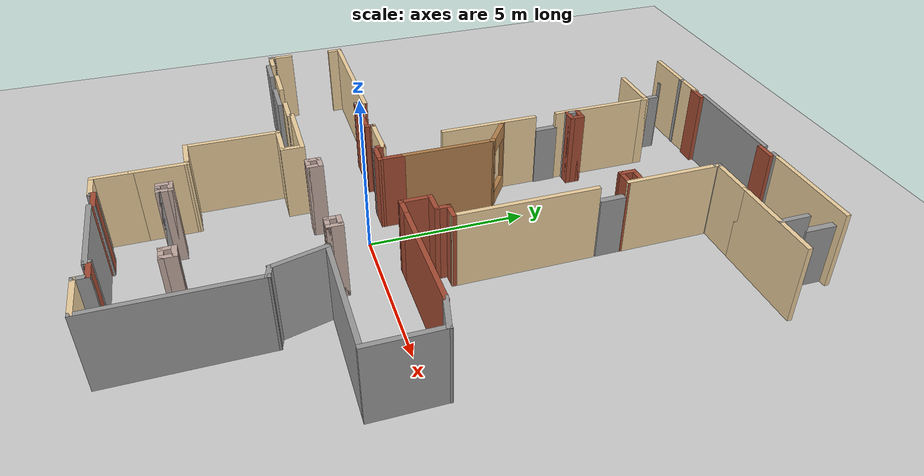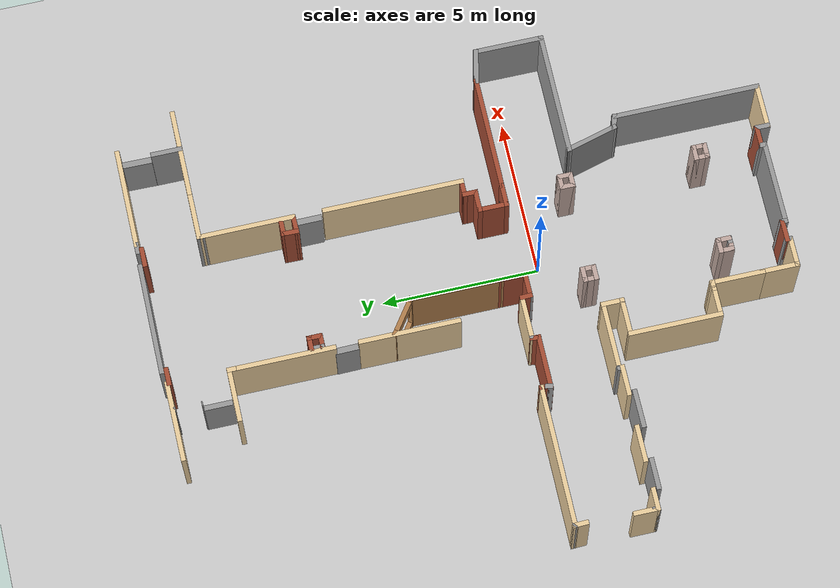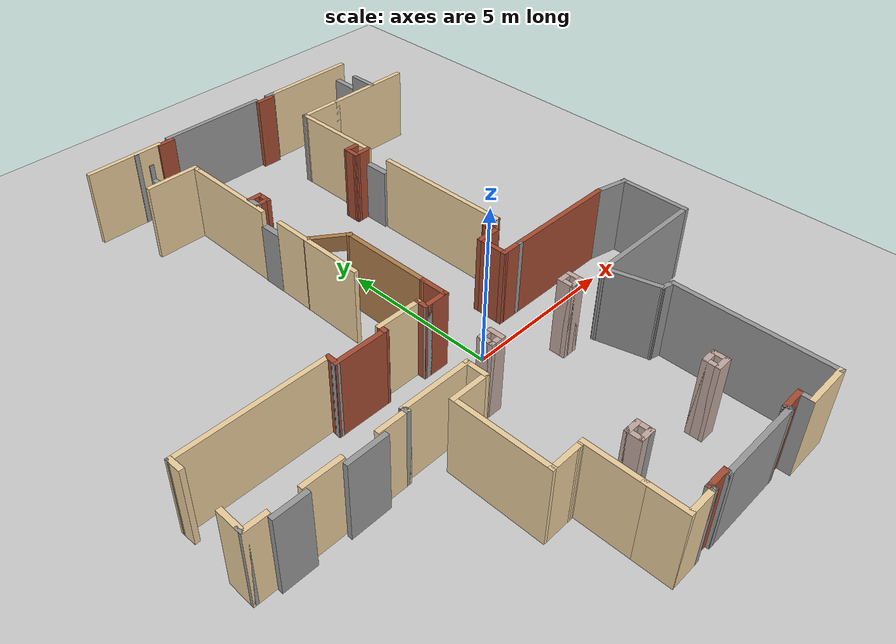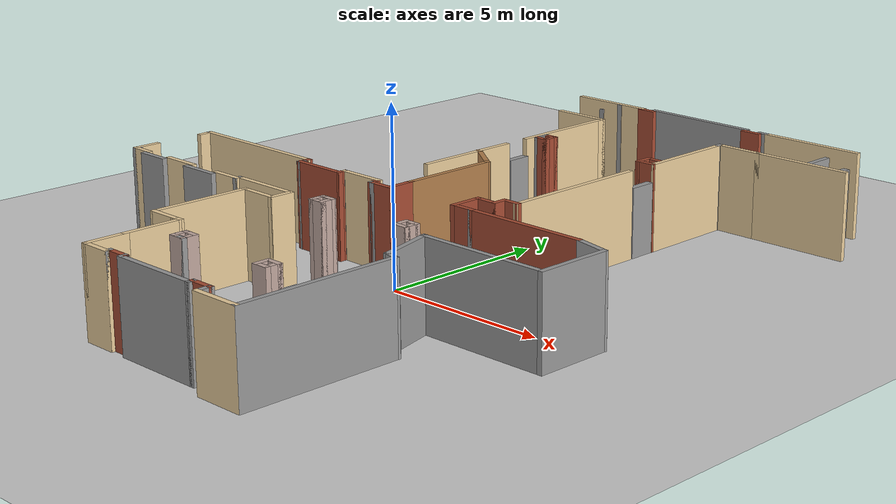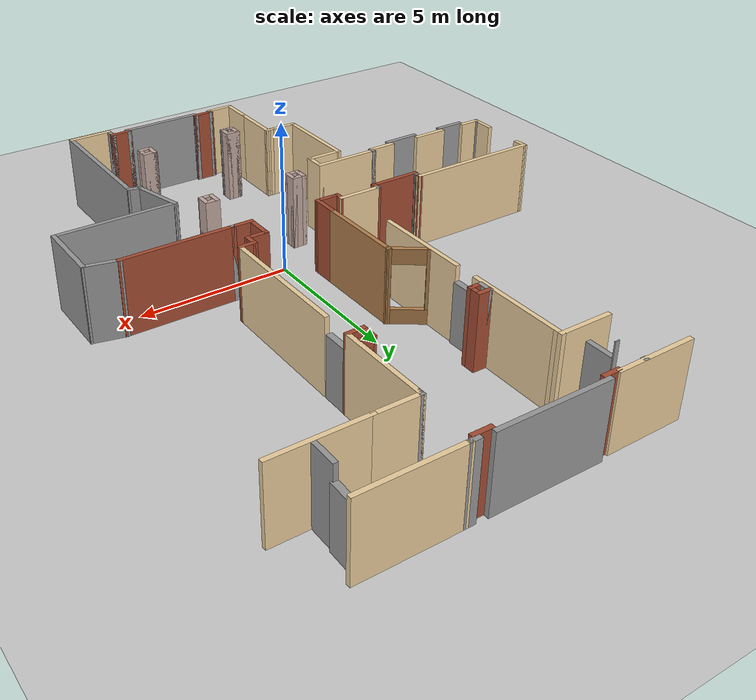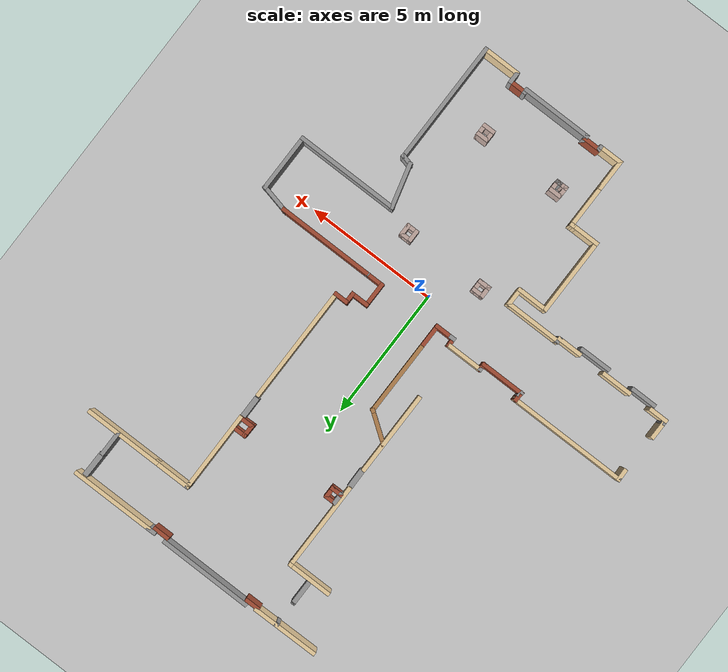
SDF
<sdf version="1.6">
 <world name="default">
  <plugin name="SpawnActorPlugin" filename="libSpawnActorPlugin.so"/>
  <model name="ground_plane">
   <static>1</static>
   <link name="link">
    <collision name="collision">
     <geometry><plane><normal>0 0 1</normal><size>100 100</size></plane></geometry>
     <surface>
      <contact><collide_bitmask>65535</collide_bitmask></contact>
      <friction><ode><mu>100</mu><mu2>50</mu2></ode></friction>
     </surface>
    </collision>
    <visual name="visual">
     <cast_shadows>0</cast_shadows>
     <geometry><plane><normal>0 0 1</normal><size>100 100</size></plane></geometry>
     <material>
      <script><uri>file://media/materials/scripts/gazebo.material</uri><name>Gazebo/Grey</name></script>
     </material>
    </visual>
   </link>
  </model>
  <gravity>0 0 -9.8</gravity>
  <magnetic_field>6e-06 2.3e-05 -4.2e-05</magnetic_field>
  <atmosphere type="adiabatic"/>
  <physics name="default_physics" default="0" type="ode">
   <max_step_size>0.001</max_step_size>
   <real_time_factor>1</real_time_factor>
   <real_time_update_rate>1000</real_time_update_rate>
  </physics>
  <scene><ambient>0.4 0.4 0.4 1</ambient><background>0.7 0.7 0.7 1</background><shadows>1</shadows></scene>
  <spherical_coordinates>
   <surface_model>EARTH_WGS84</surface_model>
   <latitude_deg>0</latitude_deg>
   <longitude_deg>0</longitude_deg>
   <elevation>0</elevation>
   <heading_deg>0</heading_deg>
  </spherical_coordinates>
  <model name="NSH_Hallway">
   <pose>-1.11426 2.16116 0 0 -0 0</pose>
   <link name="Door_5">
    <collision name="Door_5_Collision">
     <geometry><box><size>0.745301 0.2 2</size></box></geometry>
     <pose>0 0 1 0 -0 0</pose>
    </collision>
    <visual name="Door_5_Visual">
     <pose>0 0 1 0 -0 0</pose>
     <geometry><box><size>0.745301 0.2 2</size></box></geometry>
     <material>
      <script><uri>file://media/materials/scripts/gazebo.material</uri><name>Gazebo/Grey</name></script>
     </material>
    </visual>
    <pose>-0.72798 4.33452 0 0 -0 1.58636</pose>
   </link>
   <link name="Door_6">
    <collision name="Door_6_Collision">
     <geometry><box><size>0.80689 0.2 2</size></box></geometry>
     <pose>0 0 1 0 -0 0</pose>
    </collision>
    <visual name="Door_6_Visual">
     <pose>0 0 1 0 -0 0</pose>
     <geometry><box><size>0.80689 0.2 2</size></box></geometry>
     <material>
      <script><uri>file://media/materials/scripts/gazebo.material</uri><name>Gazebo/Grey</name></script>
     </material>
    </visual>
    <pose>3.65842 4.59476 0 0 -0 -1.56651</pose>
   </link>
   <link name="Door_7">
    <collision name="Door_7_Collision">
     <geometry><box><size>0.9 0.17 2</size></box></geometry>
     <pose>0 0 1 0 -0 0</pose>
    </collision>
    <visual name="Door_7_Visual">
     <pose>0 0 1 0 -0 0</pose>
     <geometry><box><size>0.9 0.17 2</size></box></geometry>
     <material>
      <script><uri>file://media/materials/scripts/gazebo.material</uri><name>Gazebo/Grey</name></script>
     </material>
    </visual>
    <pose>-1.62302 8.5531 0 0 -0 1.5718</pose>
   </link>
   <link name="Door_8">
    <collision name="Door_8_Collision">
     <geometry><box><size>1.0376 0.2 2</size></box></geometry>
     <pose>0 0 1 0 -0 0</pose>
    </collision>
    <visual name="Door_8_Visual">
     <pose>0 0 1 0 -0 0</pose>
     <geometry><box><size>1.0376 0.2 2</size></box></geometry>
     <material>
      <script><uri>file://media/materials/scripts/gazebo.material</uri><name>Gazebo/Grey</name></script>
     </material>
    </visual>
    <pose>6.70761 9.4487 0 0 -0 -1.58386</pose>
   </link>
   <link name="Wall_102">
    <collision name="Wall_102_Collision">
     <geometry><box><size>0.563182 0.15 2.5</size></box></geometry>
     <pose>0 0 1.25 0 -0 0</pose>
    </collision>
    <visual name="Wall_102_Visual">
     <pose>0 0 1.25 0 -0 0</pose>
     <geometry><box><size>0.563182 0.15 2.5</size></box></geometry>
     <material>
      <script><uri>file://media/materials/scripts/gazebo.material</uri><name>Gazebo/Bricks</name></script>
      <ambient>1 1 1 1</ambient>
     </material>
     <meta><layer>0</layer></meta>
    </visual>
    <pose>3.20361 5.2674 0 0 -0 -1.58529</pose>
   </link>
   <link name="Wall_103">
    <collision name="Wall_103_Collision">
     <geometry><box><size>0.64071 0.15 2.5</size></box></geometry>
     <pose>0 0 1.25 0 -0 0</pose>
    </collision>
    <visual name="Wall_103_Visual">
     <pose>0 0 1.25 0 -0 0</pose>
     <geometry><box><size>0.64071 0.15 2.5</size></box></geometry>
     <material>
      <script><uri>file://media/materials/scripts/gazebo.material</uri><name>Gazebo/Bricks</name></script>
      <ambient>1 1 1 1</ambient>
     </material>
     <meta><layer>0</layer></meta>
    </visual>
    <pose>3.4459 5.06699 0 0 -0 0.024385</pose>
   </link>
   <link name="Wall_105">
    <collision name="Wall_105_Collision">
     <geometry><box><size>0.75 0.15 2.5</size></box></geometry>
     <pose>0 0 1.25 0 -0 0</pose>
    </collision>
    <visual name="Wall_105_Visual">
     <pose>0 0 1.25 0 -0 0</pose>
     <geometry><box><size>0.75 0.15 2.5</size></box></geometry>
     <material>
      <script><uri>file://media/materials/scripts/gazebo.material</uri><name>Gazebo/Grey</name></script>
      <ambient>0.921569 0.807843 0.615686 1</ambient>
     </material>
     <meta><layer>0</layer></meta>
    </visual>
    <pose>-7.88142 -3.32378 0 0 -0 -1.5708</pose>
   </link>
   <link name="Wall_106">
    <collision name="Wall_106_Collision">
     <geometry><box><size>0.25 0.15 2.5</size></box></geometry>
     <pose>0 0 1.25 0 -0 0</pose>
    </collision>
    <visual name="Wall_106_Visual">
     <pose>0 0 1.25 0 -0 0</pose>
     <geometry><box><size>0.25 0.15 2.5</size></box></geometry>
     <material>
      <script><uri>file://media/materials/scripts/gazebo.material</uri><name>Gazebo/Grey</name></script>
      <ambient>1 1 1 1</ambient>
     </material>
     <meta><layer>0</layer></meta>
    </visual>
    <pose>-7.88142 -3.67378 0 0 -0 -1.5708</pose>
   </link>
   <link name="Wall_107">
    <collision name="Wall_107_Collision">
     <geometry><box><size>0.75 0.15 2.5</size></box></geometry>
     <pose>0 0 1.25 0 -0 0</pose>
    </collision>
    <visual name="Wall_107_Visual">
     <pose>0 0 1.25 0 -0 0</pose>
     <geometry><box><size>0.75 0.15 2.5</size></box></geometry>
     <material>
      <script><uri>file://media/materials/scripts/gazebo.material</uri><name>Gazebo/Grey</name></script>
      <ambient>0.921569 0.807843 0.615686 1</ambient>
     </material>
     <meta><layer>0</layer></meta>
    </visual>
    <pose>-7.58142 -3.72378 0 0 -0 0</pose>
   </link>
   <link name="Wall_109">
    <collision name="Wall_109_Collision">
     <geometry><box><size>1.19955 0.15 2.5</size></box></geometry>
     <pose>0 0 1.25 0 -0 0</pose>
    </collision>
    <visual name="Wall_109_Visual">
     <pose>0 0 1.25 0 -0 0</pose>
     <geometry><box><size>1.19955 0.15 2.5</size></box></geometry>
     <material>
      <script><uri>file://media/materials/scripts/gazebo.material</uri><name>Gazebo/Grey</name></script>
      <ambient>0.921569 0.807843 0.615686 1</ambient>
     </material>
     <meta><layer>0</layer></meta>
    </visual>
    <pose>-5.78849 -3.71137 0 0 -0 0</pose>
   </link>
   <link name="Wall_17">
    <collision name="Wall_17_Collision">
     <geometry><box><size>4.5 0.15 2.5</size></box></geometry>
     <pose>0 0 1.25 0 -0 0</pose>
    </collision>
    <visual name="Wall_17_Visual">
     <pose>0 0 1.25 0 -0 0</pose>
     <geometry><box><size>4.5 0.15 2.5</size></box></geometry>
     <material>
      <script><uri>file://media/materials/scripts/gazebo.material</uri><name>Gazebo/Grey</name></script>
      <ambient>0.921569 0.807843 0.615686 1</ambient>
     </material>
     <meta><layer>0</layer></meta>
    </visual>
    <pose>3.6845 1.90132 0 0 -0 -1.5708</pose>
   </link>
   <link name="Wall_172">
    <collision name="Wall_172_Collision">
     <geometry><box><size>1.25 0.15 2.5</size></box></geometry>
     <pose>0 0 1.25 0 -0 0</pose>
    </collision>
    <visual name="Wall_172_Visual">
     <pose>0 0 1.25 0 -0 0</pose>
     <geometry><box><size>1.25 0.15 2.5</size></box></geometry>
     <material>
      <script><uri>file://media/materials/scripts/gazebo.material</uri><name>Gazebo/Grey</name></script>
      <ambient>0.921569 0.807843 0.615686 1</ambient>
     </material>
     <meta><layer>0</layer></meta>
    </visual>
    <pose>-1.76247 -4.22776 0 0 -0 3.14144</pose>
   </link>
   <link name="Wall_173">
    <collision name="Wall_173_Collision">
     <geometry><box><size>3 0.15 2.5</size></box></geometry>
     <pose>0 0 1.25 0 -0 0</pose>
    </collision>
    <visual name="Wall_173_Visual">
     <pose>0 0 1.25 0 -0 0</pose>
     <geometry><box><size>3 0.15 2.5</size></box></geometry>
     <material>
      <script><uri>file://media/materials/scripts/gazebo.material</uri><name>Gazebo/Grey</name></script>
      <ambient>0.921569 0.807843 0.615686 1</ambient>
     </material>
     <meta><layer>0</layer></meta>
    </visual>
    <pose>-2.3125 -5.65268 0 0 -0 -1.5708</pose>
   </link>
   <link name="Wall_174">
    <collision name="Wall_174_Collision">
     <geometry><box><size>1 0.15 2.5</size></box></geometry>
     <pose>0 0 1.25 0 -0 0</pose>
    </collision>
    <visual name="Wall_174_Visual">
     <pose>0 0 1.25 0 -0 0</pose>
     <geometry><box><size>1 0.15 2.5</size></box></geometry>
     <material>
      <script><uri>file://media/materials/scripts/gazebo.material</uri><name>Gazebo/Grey</name></script>
      <ambient>0.921569 0.807843 0.615686 1</ambient>
     </material>
     <meta><layer>0</layer></meta>
    </visual>
    <pose>-1.88747 -7.07776 0 0 -0 -0.000198</pose>
   </link>
   <link name="Wall_175">
    <collision name="Wall_175_Collision">
     <geometry><box><size>0.349388 0.15 2.5</size></box></geometry>
     <pose>0 0 1.25 0 -0 0</pose>
    </collision>
    <visual name="Wall_175_Visual">
     <pose>0 0 1.25 0 -0 0</pose>
     <geometry><box><size>0.349388 0.15 2.5</size></box></geometry>
     <material>
      <script><uri>file://media/materials/scripts/gazebo.material</uri><name>Gazebo/Grey</name></script>
      <ambient>0.921569 0.807843 0.615686 1</ambient>
     </material>
     <meta><layer>0</layer></meta>
    </visual>
    <pose>-1.36276 -7.07686 0 0 -0 0.009857</pose>
   </link>
   <link name="Wall_176">
    <collision name="Wall_176_Collision">
     <geometry><box><size>1.75 0.15 2.5</size></box></geometry>
     <pose>0 0 1.25 0 -0 0</pose>
    </collision>
    <visual name="Wall_176_Visual">
     <pose>0 0 1.25 0 -0 0</pose>
     <geometry><box><size>1.75 0.15 2.5</size></box></geometry>
     <material>
      <script><uri>file://media/materials/scripts/gazebo.material</uri><name>Gazebo/Grey</name></script>
      <ambient>0.921569 0.807843 0.615686 1</ambient>
     </material>
     <meta><layer>0</layer></meta>
    </visual>
    <pose>-1.26307 -7.87588 0 0 -0 -1.5708</pose>
   </link>
   <link name="Wall_179">
    <collision name="Wall_179_Collision">
     <geometry><box><size>0.5 0.15 2.5</size></box></geometry>
     <pose>0 0 1.25 0 -0 0</pose>
    </collision>
    <visual name="Wall_179_Visual">
     <pose>0 0 1.25 0 -0 0</pose>
     <geometry><box><size>0.5 0.15 2.5</size></box></geometry>
     <material>
      <script><uri>file://media/materials/scripts/gazebo.material</uri><name>Gazebo/Grey</name></script>
      <ambient>0.760784 0.662745 0.627451 1</ambient>
     </material>
     <meta><layer>0</layer></meta>
    </visual>
    <pose>-0.146646 -7.58829 0 0 -0 0</pose>
   </link>
   <link name="Wall_180">
    <collision name="Wall_180_Collision">
     <geometry><box><size>0.5 0.15 2.5</size></box></geometry>
     <pose>0 0 1.25 0 -0 0</pose>
    </collision>
    <visual name="Wall_180_Visual">
     <pose>0 0 1.25 0 -0 0</pose>
     <geometry><box><size>0.5 0.15 2.5</size></box></geometry>
     <material>
      <script><uri>file://media/materials/scripts/gazebo.material</uri><name>Gazebo/Grey</name></script>
      <ambient>0.760784 0.662745 0.627451 1</ambient>
     </material>
     <meta><layer>0</layer></meta>
    </visual>
    <pose>0.028354 -7.76329 0 0 -0 -1.5708</pose>
   </link>
   <link name="Wall_181">
    <collision name="Wall_181_Collision">
     <geometry><box><size>0.25 0.15 2.5</size></box></geometry>
     <pose>0 0 1.25 0 -0 0</pose>
    </collision>
    <visual name="Wall_181_Visual">
     <pose>0 0 1.25 0 -0 0</pose>
     <geometry><box><size>0.25 0.15 2.5</size></box></geometry>
     <material>
      <script><uri>file://media/materials/scripts/gazebo.material</uri><name>Gazebo/Grey</name></script>
      <ambient>1 1 1 1</ambient>
     </material>
     <meta><layer>0</layer></meta>
    </visual>
    <pose>-0.021646 -7.9383 0 0 -0 3.14159</pose>
   </link>
   <link name="Wall_183">
    <collision name="Wall_183_Collision">
     <geometry><box><size>0.5 0.15 2.5</size></box></geometry>
     <pose>0 0 1.25 0 -0 0</pose>
    </collision>
    <visual name="Wall_183_Visual">
     <pose>0 0 1.25 0 -0 0</pose>
     <geometry><box><size>0.5 0.15 2.5</size></box></geometry>
     <material>
      <script><uri>file://media/materials/scripts/gazebo.material</uri><name>Gazebo/Grey</name></script>
      <ambient>0.760784 0.662745 0.627451 1</ambient>
     </material>
     <meta><layer>0</layer></meta>
    </visual>
    <pose>-0.321646 -7.76329 0 0 -0 -1.5708</pose>
   </link>
   <link name="Wall_184">
    <collision name="Wall_184_Collision">
     <geometry><box><size>0.5 0.15 2.5</size></box></geometry>
     <pose>0 0 1.25 0 -0 0</pose>
    </collision>
    <visual name="Wall_184_Visual">
     <pose>0 0 1.25 0 -0 0</pose>
     <geometry><box><size>0.5 0.15 2.5</size></box></geometry>
     <material>
      <script><uri>file://media/materials/scripts/gazebo.material</uri><name>Gazebo/Grey</name></script>
      <ambient>0.760784 0.662745 0.627451 1</ambient>
     </material>
     <meta><layer>0</layer></meta>
    </visual>
    <pose>-0.146646 -7.9383 0 0 -0 0</pose>
   </link>
   <link name="Wall_186">
    <collision name="Wall_186_Collision">
     <geometry><box><size>0.5 0.15 2.5</size></box></geometry>
     <pose>0 0 1.25 0 -0 0</pose>
    </collision>
    <visual name="Wall_186_Visual">
     <pose>0 0 1.25 0 -0 0</pose>
     <geometry><box><size>0.5 0.15 2.5</size></box></geometry>
     <material>
      <script><uri>file://media/materials/scripts/gazebo.material</uri><name>Gazebo/Grey</name></script>
      <ambient>0.760784 0.662745 0.627451 1</ambient>
     </material>
     <meta><layer>0</layer></meta>
    </visual>
    <pose>2.99841 -7.58829 0 0 -0 0</pose>
   </link>
   <link name="Wall_187">
    <collision name="Wall_187_Collision">
     <geometry><box><size>0.5 0.15 2.5</size></box></geometry>
     <pose>0 0 1.25 0 -0 0</pose>
    </collision>
    <visual name="Wall_187_Visual">
     <pose>0 0 1.25 0 -0 0</pose>
     <geometry><box><size>0.5 0.15 2.5</size></box></geometry>
     <material>
      <script><uri>file://media/materials/scripts/gazebo.material</uri><name>Gazebo/Grey</name></script>
      <ambient>0.760784 0.662745 0.627451 1</ambient>
     </material>
     <meta><layer>0</layer></meta>
    </visual>
    <pose>3.17341 -7.76329 0 0 -0 -1.5708</pose>
   </link>
   <link name="Wall_188">
    <collision name="Wall_188_Collision">
     <geometry><box><size>0.5 0.15 2.5</size></box></geometry>
     <pose>0 0 1.25 0 -0 0</pose>
    </collision>
    <visual name="Wall_188_Visual">
     <pose>0 0 1.25 0 -0 0</pose>
     <geometry><box><size>0.5 0.15 2.5</size></box></geometry>
     <material>
      <script><uri>file://media/materials/scripts/gazebo.material</uri><name>Gazebo/Grey</name></script>
      <ambient>0.760784 0.662745 0.627451 1</ambient>
     </material>
     <meta><layer>0</layer></meta>
    </visual>
    <pose>2.99841 -7.9383 0 0 -0 3.14159</pose>
   </link>
   <link name="Wall_189">
    <collision name="Wall_189_Collision">
     <geometry><box><size>0.5 0.15 2.5</size></box></geometry>
     <pose>0 0 1.25 0 -0 0</pose>
    </collision>
    <visual name="Wall_189_Visual">
     <pose>0 0 1.25 0 -0 0</pose>
     <geometry><box><size>0.5 0.15 2.5</size></box></geometry>
     <material>
      <script><uri>file://media/materials/scripts/gazebo.material</uri><name>Gazebo/Grey</name></script>
      <ambient>0.760784 0.662745 0.627451 1</ambient>
     </material>
     <meta><layer>0</layer></meta>
    </visual>
    <pose>2.82341 -7.76329 0 0 -0 1.5708</pose>
   </link>
   <link name="Wall_191">
    <collision name="Wall_191_Collision">
     <geometry><box><size>1.25 0.15 2.5</size></box></geometry>
     <pose>0 0 1.25 0 -0 0</pose>
    </collision>
    <visual name="Wall_191_Visual">
     <pose>0 0 1.25 0 -0 0</pose>
     <geometry><box><size>1.25 0.15 2.5</size></box></geometry>
     <material>
      <script><uri>file://media/materials/scripts/gazebo.material</uri><name>Gazebo/Grey</name></script>
      <ambient>0.921569 0.807843 0.615686 1</ambient>
     </material>
     <meta><layer>0</layer></meta>
    </visual>
    <pose>-1.26307 -9.22588 0 0 -0 -1.5708</pose>
   </link>
   <link name="Wall_192">
    <collision name="Wall_192_Collision">
     <geometry><box><size>1 0.15 2.5</size></box></geometry>
     <pose>0 0 1.25 0 -0 0</pose>
    </collision>
    <visual name="Wall_192_Visual">
     <pose>0 0 1.25 0 -0 0</pose>
     <geometry><box><size>1 0.15 2.5</size></box></geometry>
     <material>
      <script><uri>file://media/materials/scripts/gazebo.material</uri><name>Gazebo/Grey</name></script>
      <ambient>0.921569 0.807843 0.615686 1</ambient>
     </material>
     <meta><layer>0</layer></meta>
    </visual>
    <pose>-0.838069 -9.77588 0 0 -0 0</pose>
   </link>
   <link name="Wall_193">
    <collision name="Wall_193_Collision">
     <geometry><box><size>0.15 0.15 2.5</size></box></geometry>
     <pose>0 0 1.25 0 -0 0</pose>
    </collision>
    <visual name="Wall_193_Visual">
     <pose>0 0 1.25 0 -0 0</pose>
     <geometry><box><size>0.15 0.15 2.5</size></box></geometry>
     <material>
      <script><uri>file://media/materials/scripts/gazebo.material</uri><name>Gazebo/Grey</name></script>
      <ambient>1 1 1 1</ambient>
     </material>
     <meta><layer>0</layer></meta>
    </visual>
    <pose>-0.413069 -9.77588 0 0 -0 0</pose>
   </link>
   <link name="Wall_194">
    <collision name="Wall_194_Collision">
     <geometry><box><size>0.25 0.15 2.5</size></box></geometry>
     <pose>0 0 1.25 0 -0 0</pose>
    </collision>
    <visual name="Wall_194_Visual">
     <pose>0 0 1.25 0 -0 0</pose>
     <geometry><box><size>0.25 0.15 2.5</size></box></geometry>
     <material>
      <script><uri>file://media/materials/scripts/gazebo.material</uri><name>Gazebo/Grey</name></script>
      <ambient>1 1 1 1</ambient>
     </material>
     <meta><layer>0</layer></meta>
    </visual>
    <pose>-0.413069 -9.72588 0 0 -0 1.5708</pose>
   </link>
   <link name="Wall_195">
    <collision name="Wall_195_Collision">
     <geometry><box><size>0.75 0.15 2.5</size></box></geometry>
     <pose>0 0 1.25 0 -0 0</pose>
    </collision>
    <visual name="Wall_195_Visual">
     <pose>0 0 1.25 0 -0 0</pose>
     <geometry><box><size>0.75 0.15 2.5</size></box></geometry>
     <material>
      <script><uri>file://media/materials/scripts/gazebo.material</uri><name>Gazebo/Bricks</name></script>
      <ambient>1 1 1 1</ambient>
     </material>
     <meta><layer>0</layer></meta>
    </visual>
    <pose>-0.113069 -9.67588 0 0 -0 0</pose>
   </link>
   <link name="Wall_196">
    <collision name="Wall_196_Collision">
     <geometry><box><size>0.25 0.15 2.5</size></box></geometry>
     <pose>0 0 1.25 0 -0 0</pose>
    </collision>
    <visual name="Wall_196_Visual">
     <pose>0 0 1.25 0 -0 0</pose>
     <geometry><box><size>0.25 0.15 2.5</size></box></geometry>
     <material>
      <script><uri>file://media/materials/scripts/gazebo.material</uri><name>Gazebo/Grey</name></script>
      <ambient>1 1 1 1</ambient>
     </material>
     <meta><layer>0</layer></meta>
    </visual>
    <pose>0.186931 -9.72588 0 0 -0 -1.5708</pose>
   </link>
   <link name="Wall_197">
    <collision name="Wall_197_Collision">
     <geometry><box><size>2.75 0.15 2.5</size></box></geometry>
     <pose>0 0 1.25 0 -0 0</pose>
    </collision>
    <visual name="Wall_197_Visual">
     <pose>0 0 1.25 0 -0 0</pose>
     <geometry><box><size>2.75 0.15 2.5</size></box></geometry>
     <material>
      <script><uri>file://media/materials/scripts/gazebo.material</uri><name>Gazebo/Grey</name></script>
      <ambient>0.333333 0.341176 0.32549 1</ambient>
     </material>
     <meta><layer>0</layer></meta>
    </visual>
    <pose>1.48693 -9.77588 0 0 -0 0</pose>
   </link>
   <link name="Wall_198">
    <collision name="Wall_198_Collision">
     <geometry><box><size>0.25 0.15 2.5</size></box></geometry>
     <pose>0 0 1.25 0 -0 0</pose>
    </collision>
    <visual name="Wall_198_Visual">
     <pose>0 0 1.25 0 -0 0</pose>
     <geometry><box><size>0.25 0.15 2.5</size></box></geometry>
     <material>
      <script><uri>file://media/materials/scripts/gazebo.material</uri><name>Gazebo/Grey</name></script>
      <ambient>1 1 1 1</ambient>
     </material>
     <meta><layer>0</layer></meta>
    </visual>
    <pose>2.78693 -9.72588 0 0 -0 1.5708</pose>
   </link>
   <link name="Wall_199">
    <collision name="Wall_199_Collision">
     <geometry><box><size>0.75 0.15 2.5</size></box></geometry>
     <pose>0 0 1.25 0 -0 0</pose>
    </collision>
    <visual name="Wall_199_Visual">
     <pose>0 0 1.25 0 -0 0</pose>
     <geometry><box><size>0.75 0.15 2.5</size></box></geometry>
     <material>
      <script><uri>file://media/materials/scripts/gazebo.material</uri><name>Gazebo/Bricks</name></script>
      <ambient>1 1 1 1</ambient>
     </material>
     <meta><layer>0</layer></meta>
    </visual>
    <pose>3.08693 -9.67588 0 0 -0 0</pose>
   </link>
   <link name="Wall_20">
    <collision name="Wall_20_Collision">
     <geometry><box><size>0.597367 0.15 2.5</size></box></geometry>
     <pose>0 0 1.25 0 -0 0</pose>
    </collision>
    <visual name="Wall_20_Visual">
     <pose>0 0 1.25 0 -0 0</pose>
     <geometry><box><size>0.597367 0.15 2.5</size></box></geometry>
     <material>
      <script><uri>file://media/materials/scripts/gazebo.material</uri><name>Gazebo/Bricks</name></script>
      <ambient>1 1 1 1</ambient>
     </material>
     <meta><layer>0</layer></meta>
    </visual>
    <pose>3.461 -0.27268 0 0 -0 3.13712</pose>
   </link>
   <link name="Wall_200">
    <collision name="Wall_200_Collision">
     <geometry><box><size>0.5 0.15 2.5</size></box></geometry>
     <pose>0 0 1.25 0 -0 0</pose>
    </collision>
    <visual name="Wall_200_Visual">
     <pose>0 0 1.25 0 -0 0</pose>
     <geometry><box><size>0.5 0.15 2.5</size></box></geometry>
     <material>
      <script><uri>file://media/materials/scripts/gazebo.material</uri><name>Gazebo/Grey</name></script>
      <ambient>1 1 1 1</ambient>
     </material>
     <meta><layer>0</layer></meta>
    </visual>
    <pose>3.38693 -9.85088 0 0 -0 -1.5708</pose>
   </link>
   <link name="Wall_201">
    <collision name="Wall_201_Collision">
     <geometry><box><size>1.5 0.15 2.5</size></box></geometry>
     <pose>0 0 1.25 0 -0 0</pose>
    </collision>
    <visual name="Wall_201_Visual">
     <pose>0 0 1.25 0 -0 0</pose>
     <geometry><box><size>1.5 0.15 2.5</size></box></geometry>
     <material>
      <script><uri>file://media/materials/scripts/gazebo.material</uri><name>Gazebo/Grey</name></script>
      <ambient>0.921569 0.807843 0.615686 1</ambient>
     </material>
     <meta><layer>0</layer></meta>
    </visual>
    <pose>4.06193 -10.0259 0 0 -0 0</pose>
   </link>
   <link name="Wall_203">
    <collision name="Wall_203_Collision">
     <geometry><box><size>0.5 0.15 2.5</size></box></geometry>
     <pose>0 0 1.25 0 -0 0</pose>
    </collision>
    <visual name="Wall_203_Visual">
     <pose>0 0 1.25 0 -0 0</pose>
     <geometry><box><size>0.5 0.15 2.5</size></box></geometry>
     <material>
      <script><uri>file://media/materials/scripts/gazebo.material</uri><name>Gazebo/Grey</name></script>
      <ambient>0.760784 0.662745 0.627451 1</ambient>
     </material>
     <meta><layer>0</layer></meta>
    </visual>
    <pose>-0.14273 -3.2766 0 0 -0 0</pose>
   </link>
   <link name="Wall_204">
    <collision name="Wall_204_Collision">
     <geometry><box><size>0.5 0.15 2.5</size></box></geometry>
     <pose>0 0 1.25 0 -0 0</pose>
    </collision>
    <visual name="Wall_204_Visual">
     <pose>0 0 1.25 0 -0 0</pose>
     <geometry><box><size>0.5 0.15 2.5</size></box></geometry>
     <material>
      <script><uri>file://media/materials/scripts/gazebo.material</uri><name>Gazebo/Grey</name></script>
      <ambient>0.760784 0.662745 0.627451 1</ambient>
     </material>
     <meta><layer>0</layer></meta>
    </visual>
    <pose>0.03227 -3.4516 0 0 -0 -1.5708</pose>
   </link>
   <link name="Wall_205">
    <collision name="Wall_205_Collision">
     <geometry><box><size>0.5 0.15 2.5</size></box></geometry>
     <pose>0 0 1.25 0 -0 0</pose>
    </collision>
    <visual name="Wall_205_Visual">
     <pose>0 0 1.25 0 -0 0</pose>
     <geometry><box><size>0.5 0.15 2.5</size></box></geometry>
     <material>
      <script><uri>file://media/materials/scripts/gazebo.material</uri><name>Gazebo/Grey</name></script>
      <ambient>0.760784 0.662745 0.627451 1</ambient>
     </material>
     <meta><layer>0</layer></meta>
    </visual>
    <pose>-0.14273 -3.6266 0 0 -0 3.14159</pose>
   </link>
   <link name="Wall_206">
    <collision name="Wall_206_Collision">
     <geometry><box><size>0.5 0.15 2.5</size></box></geometry>
     <pose>0 0 1.25 0 -0 0</pose>
    </collision>
    <visual name="Wall_206_Visual">
     <pose>0 0 1.25 0 -0 0</pose>
     <geometry><box><size>0.5 0.15 2.5</size></box></geometry>
     <material>
      <script><uri>file://media/materials/scripts/gazebo.material</uri><name>Gazebo/Grey</name></script>
      <ambient>0.760784 0.662745 0.627451 1</ambient>
     </material>
     <meta><layer>0</layer></meta>
    </visual>
    <pose>-0.31773 -3.4516 0 0 -0 1.5708</pose>
   </link>
   <link name="Wall_208">
    <pose>-1.61648 9.49659 0 0 -0 -1.5708</pose>
    <visual name="Wall_208_Visual_0">
     <pose>-0.419604 0 1.25 0 -0 0</pose>
     <geometry><box><size>0.160793 0.15 2.5</size></box></geometry>
     <material>
      <script><uri>file://media/materials/scripts/gazebo.material</uri><name>Gazebo/Grey</name></script>
      <ambient>1 1 1 1</ambient>
     </material>
     <meta><layer>0</layer></meta>
    </visual>
    <collision name="Wall_208_Collision_0">
     <geometry><box><size>0.160793 0.15 2.5</size></box></geometry>
     <pose>-0.419604 0 1.25 0 -0 0</pose>
    </collision>
    <visual name="Wall_208_Visual_1">
     <pose>0.480396 0 1.25 0 -0 0</pose>
     <geometry><box><size>0.039207 0.15 2.5</size></box></geometry>
     <material>
      <script><uri>file://media/materials/scripts/gazebo.material</uri><name>Gazebo/Grey</name></script>
      <ambient>1 1 1 1</ambient>
     </material>
     <meta><layer>0</layer></meta>
    </visual>
    <collision name="Wall_208_Collision_1">
     <geometry><box><size>0.039207 0.15 2.5</size></box></geometry>
     <pose>0.480396 0 1.25 0 -0 0</pose>
    </collision>
   </link>
   <link name="Wall_21">
    <collision name="Wall_21_Collision">
     <geometry><box><size>0.5 0.15 2.5</size></box></geometry>
     <pose>0 0 1.25 0 -0 0</pose>
    </collision>
    <visual name="Wall_21_Visual">
     <pose>0 0 1.25 0 -0 0</pose>
     <geometry><box><size>0.5 0.15 2.5</size></box></geometry>
     <material>
      <script><uri>file://media/materials/scripts/gazebo.material</uri><name>Gazebo/Bricks</name></script>
      <ambient>1 1 1 1</ambient>
     </material>
     <meta><layer>0</layer></meta>
    </visual>
    <pose>3.2375 -0.44668 0 0 -0 -1.5708</pose>
   </link>
   <link name="Wall_213">
    <collision name="Wall_213_Collision">
     <geometry><box><size>1.01832 0.15 2.5</size></box></geometry>
     <pose>0 0 1.25 0 -0 0</pose>
    </collision>
    <visual name="Wall_213_Visual">
     <pose>0 0 1.25 0 -0 0</pose>
     <geometry><box><size>1.01832 0.15 2.5</size></box></geometry>
     <material>
      <script><uri>file://media/materials/scripts/gazebo.material</uri><name>Gazebo/Grey</name></script>
      <ambient>0.180392 0.203922 0.211765 1</ambient>
     </material>
     <meta><layer>0</layer></meta>
    </visual>
    <pose>-6.80225 -3.89503 0 0 -0 3.14159</pose>
   </link>
   <link name="Wall_217">
    <collision name="Wall_217_Collision">
     <geometry><box><size>1.24518 0.15 2.5</size></box></geometry>
     <pose>0 0 1.25 0 -0 0</pose>
    </collision>
    <visual name="Wall_217_Visual">
     <pose>0 0 1.25 0 -0 0</pose>
     <geometry><box><size>1.24518 0.15 2.5</size></box></geometry>
     <material>
      <script><uri>file://media/materials/scripts/gazebo.material</uri><name>Gazebo/Grey</name></script>
      <ambient>0.333333 0.341176 0.32549 1</ambient>
     </material>
     <meta><layer>0</layer></meta>
    </visual>
    <pose>-4.70184 -3.91458 0 0 -0 -3.13445</pose>
   </link>
   <link name="Wall_219">
    <collision name="Wall_219_Collision">
     <geometry><box><size>4.75 0.15 2.5</size></box></geometry>
     <pose>0 0 1.25 0 -0 0</pose>
    </collision>
    <visual name="Wall_219_Visual">
     <pose>0 0 1.25 0 -0 0</pose>
     <geometry><box><size>4.75 0.15 2.5</size></box></geometry>
     <material>
      <script><uri>file://media/materials/scripts/gazebo.material</uri><name>Gazebo/Grey</name></script>
      <ambient>0.180392 0.203922 0.211765 1</ambient>
     </material>
     <meta><layer>0</layer></meta>
    </visual>
    <pose>4.73693 -7.72588 0 0 -0 1.5708</pose>
   </link>
   <link name="Wall_22">
    <collision name="Wall_22_Collision">
     <geometry><box><size>0.75 0.15 2.5</size></box></geometry>
     <pose>0 0 1.25 0 -0 0</pose>
    </collision>
    <visual name="Wall_22_Visual">
     <pose>0 0 1.25 0 -0 0</pose>
     <geometry><box><size>0.75 0.15 2.5</size></box></geometry>
     <material>
      <script><uri>file://media/materials/scripts/gazebo.material</uri><name>Gazebo/Bricks</name></script>
      <ambient>1 1 1 1</ambient>
     </material>
     <meta><layer>0</layer></meta>
    </visual>
    <pose>2.9375 -0.62168 0 0 -0 3.14159</pose>
   </link>
   <link name="Wall_220">
    <collision name="Wall_220_Collision">
     <geometry><box><size>0.5 0.15 2.5</size></box></geometry>
     <pose>0 0 1.25 0 -0 0</pose>
    </collision>
    <visual name="Wall_220_Visual">
     <pose>0 0 1.25 0 -0 0</pose>
     <geometry><box><size>0.5 0.15 2.5</size></box></geometry>
     <material>
      <script><uri>file://media/materials/scripts/gazebo.material</uri><name>Gazebo/Grey</name></script>
      <ambient>0.180392 0.203922 0.211765 1</ambient>
     </material>
     <meta><layer>0</layer></meta>
    </visual>
    <pose>4.56789 -5.38059 0 0 -0 2.87979</pose>
   </link>
   <link name="Wall_221">
    <collision name="Wall_221_Collision">
     <geometry><box><size>1.75 0.15 2.5</size></box></geometry>
     <pose>0 0 1.25 0 -0 0</pose>
    </collision>
    <visual name="Wall_221_Visual">
     <pose>0 0 1.25 0 -0 0</pose>
     <geometry><box><size>1.75 0.15 2.5</size></box></geometry>
     <material>
      <script><uri>file://media/materials/scripts/gazebo.material</uri><name>Gazebo/Grey</name></script>
      <ambient>0.180392 0.203922 0.211765 1</ambient>
     </material>
     <meta><layer>0</layer></meta>
    </visual>
    <pose>4.1918 -4.56255 0 0 -0 1.8326</pose>
   </link>
   <link name="Wall_222">
    <collision name="Wall_222_Collision">
     <geometry><box><size>4 0.15 2.5</size></box></geometry>
     <pose>0 0 1.25 0 -0 0</pose>
    </collision>
    <visual name="Wall_222_Visual">
     <pose>0 0 1.25 0 -0 0</pose>
     <geometry><box><size>4 0.15 2.5</size></box></geometry>
     <material>
      <script><uri>file://media/materials/scripts/gazebo.material</uri><name>Gazebo/Grey</name></script>
      <ambient>0.180392 0.203922 0.211765 1</ambient>
     </material>
     <meta><layer>0</layer></meta>
    </visual>
    <pose>5.90975 -3.78981 0 0 -0 0</pose>
   </link>
   <link name="Wall_223">
    <collision name="Wall_223_Collision">
     <geometry><box><size>2.25 0.15 2.5</size></box></geometry>
     <pose>0 0 1.25 0 -0 0</pose>
    </collision>
    <visual name="Wall_223_Visual">
     <pose>0 0 1.25 0 -0 0</pose>
     <geometry><box><size>2.25 0.15 2.5</size></box></geometry>
     <material>
      <script><uri>file://media/materials/scripts/gazebo.material</uri><name>Gazebo/Grey</name></script>
      <ambient>0.180392 0.203922 0.211765 1</ambient>
     </material>
     <meta><layer>0</layer></meta>
    </visual>
    <pose>7.83475 -2.73982 0 0 -0 1.5708</pose>
   </link>
   <link name="Wall_224">
    <collision name="Wall_224_Collision">
     <geometry><box><size>1.15422 0.15 2.5</size></box></geometry>
     <pose>0 0 1.25 0 -0 0</pose>
    </collision>
    <visual name="Wall_224_Visual">
     <pose>0 0 1.25 0 -0 0</pose>
     <geometry><box><size>1.15422 0.15 2.5</size></box></geometry>
     <material>
      <script><uri>file://media/materials/scripts/gazebo.material</uri><name>Gazebo/Grey</name></script>
      <ambient>0.180392 0.203922 0.211765 1</ambient>
     </material>
     <meta><layer>0</layer></meta>
    </visual>
    <pose>7.34462 -1.58075 0 0 -0 2.92263</pose>
   </link>
   <link name="Wall_227">
    <pose>-0.233746 2.45717 0 0 -0 2.52388</pose>
    <visual name="Wall_227_Visual_0">
     <pose>-0.59521 0 1.25 0 -0 0</pose>
     <geometry><box><size>0.174603 0.15 2.5</size></box></geometry>
     <material>
      <script><uri>file://media/materials/scripts/gazebo.material</uri><name>Gazebo/Wood</name></script>
      <ambient>1 1 1 1</ambient>
     </material>
     <meta><layer>0</layer></meta>
    </visual>
    <collision name="Wall_227_Collision_0">
     <geometry><box><size>0.174603 0.15 2.5</size></box></geometry>
     <pose>-0.59521 0 1.25 0 -0 0</pose>
    </collision>
    <visual name="Wall_227_Visual_1">
     <pose>0.087302 0 0.25 0 -0 0</pose>
     <geometry><box><size>1.19042 0.15 0.5</size></box></geometry>
     <material>
      <script><uri>file://media/materials/scripts/gazebo.material</uri><name>Gazebo/Wood</name></script>
      <ambient>1 1 1 1</ambient>
     </material>
     <meta><layer>0</layer></meta>
    </visual>
    <collision name="Wall_227_Collision_1">
     <geometry><box><size>1.19042 0.15 0.5</size></box></geometry>
     <pose>0.087302 0 0.25 0 -0 0</pose>
    </collision>
    <visual name="Wall_227_Visual_2">
     <pose>0.587302 0 1.5 0 -0 0</pose>
     <geometry><box><size>0.19042 0.15 2</size></box></geometry>
     <material>
      <script><uri>file://media/materials/scripts/gazebo.material</uri><name>Gazebo/Wood</name></script>
      <ambient>1 1 1 1</ambient>
     </material>
     <meta><layer>0</layer></meta>
    </visual>
    <collision name="Wall_227_Collision_2">
     <geometry><box><size>0.19042 0.15 2</size></box></geometry>
     <pose>0.587302 0 1.5 0 -0 0</pose>
    </collision>
    <visual name="Wall_227_Visual_3">
     <pose>-0.007908 0 2.25 0 -0 0</pose>
     <geometry><box><size>1 0.15 0.5</size></box></geometry>
     <material>
      <script><uri>file://media/materials/scripts/gazebo.material</uri><name>Gazebo/Wood</name></script>
      <ambient>1 1 1 1</ambient>
     </material>
     <meta><layer>0</layer></meta>
    </visual>
    <collision name="Wall_227_Collision_3">
     <geometry><box><size>1 0.15 0.5</size></box></geometry>
     <pose>-0.007908 0 2.25 0 -0 0</pose>
    </collision>
   </link>
   <link name="Wall_23">
    <collision name="Wall_23_Collision">
     <geometry><box><size>1 0.15 2.5</size></box></geometry>
     <pose>0 0 1.25 0 -0 0</pose>
    </collision>
    <visual name="Wall_23_Visual">
     <pose>0 0 1.25 0 -0 0</pose>
     <geometry><box><size>1 0.15 2.5</size></box></geometry>
     <material>
      <script><uri>file://media/materials/scripts/gazebo.material</uri><name>Gazebo/Bricks</name></script>
      <ambient>1 1 1 1</ambient>
     </material>
     <meta><layer>0</layer></meta>
    </visual>
    <pose>2.6375 -1.04668 0 0 -0 -1.5708</pose>
   </link>
   <link name="Wall_231">
    <collision name="Wall_231_Collision">
     <geometry><box><size>3.62605 0.15 2.5</size></box></geometry>
     <pose>0 0 1.25 0 -0 0</pose>
    </collision>
    <visual name="Wall_231_Visual">
     <pose>0 0 1.25 0 -0 0</pose>
     <geometry><box><size>3.62605 0.15 2.5</size></box></geometry>
     <material>
      <script><uri>file://media/materials/scripts/gazebo.material</uri><name>Gazebo/Grey</name></script>
      <ambient>0.180392 0.203922 0.211765 1</ambient>
     </material>
     <meta><layer>0</layer></meta>
    </visual>
    <pose>1.39727 10.0188 0 0 -0 -0.003914</pose>
   </link>
   <link name="Wall_24">
    <collision name="Wall_24_Collision">
     <geometry><box><size>0.776389 0.15 2.5</size></box></geometry>
     <pose>0 0 1.25 0 -0 0</pose>
    </collision>
    <visual name="Wall_24_Visual">
     <pose>0 0 1.25 0 -0 0</pose>
     <geometry><box><size>0.776389 0.15 2.5</size></box></geometry>
     <material>
      <script><uri>file://media/materials/scripts/gazebo.material</uri><name>Gazebo/Bricks</name></script>
      <ambient>1 1 1 1</ambient>
     </material>
     <meta><layer>0</layer></meta>
    </visual>
    <pose>2.9505 -1.47168 0 0 -0 0</pose>
   </link>
   <link name="Wall_25">
    <collision name="Wall_25_Collision">
     <geometry><box><size>0.15 0.15 2.5</size></box></geometry>
     <pose>0 0 1.25 0 -0 0</pose>
    </collision>
    <visual name="Wall_25_Visual">
     <pose>0 0 1.25 0 -0 0</pose>
     <geometry><box><size>0.15 0.15 2.5</size></box></geometry>
     <material>
      <script><uri>file://media/materials/scripts/gazebo.material</uri><name>Gazebo/Grey</name></script>
      <ambient>1 1 1 1</ambient>
     </material>
     <meta><layer>0</layer></meta>
    </visual>
    <pose>3.2635 -1.47168 0 0 -0 0</pose>
   </link>
   <link name="Wall_28">
    <collision name="Wall_28_Collision">
     <geometry><box><size>3.74144 0.15 2.5</size></box></geometry>
     <pose>0 0 1.25 0 -0 0</pose>
    </collision>
    <visual name="Wall_28_Visual">
     <pose>0 0 1.25 0 -0 0</pose>
     <geometry><box><size>3.74144 0.15 2.5</size></box></geometry>
     <material>
      <script><uri>file://media/materials/scripts/gazebo.material</uri><name>Gazebo/Bricks</name></script>
      <ambient>1 1 1 1</ambient>
     </material>
     <meta><layer>0</layer></meta>
    </visual>
    <pose>5.059 -1.47168 0 0 -0 0</pose>
   </link>
   <link name="Wall_31">
    <collision name="Wall_31_Collision">
     <geometry><box><size>3 0.15 2.5</size></box></geometry>
     <pose>0 0 1.25 0 -0 0</pose>
    </collision>
    <visual name="Wall_31_Visual">
     <pose>0 0 1.25 0 -0 0</pose>
     <geometry><box><size>3 0.15 2.5</size></box></geometry>
     <material>
      <script><uri>file://media/materials/scripts/gazebo.material</uri><name>Gazebo/Wood</name></script>
      <ambient>1 1 1 1</ambient>
     </material>
     <meta><layer>0</layer></meta>
    </visual>
    <pose>0.261501 0.68032 0 0 -0 1.5708</pose>
   </link>
   <link name="Wall_33">
    <collision name="Wall_33_Collision">
     <geometry><box><size>3.22621 0.15 2.5</size></box></geometry>
     <pose>0 0 1.25 0 -0 0</pose>
    </collision>
    <visual name="Wall_33_Visual">
     <pose>0 0 1.25 0 -0 0</pose>
     <geometry><box><size>3.22621 0.15 2.5</size></box></geometry>
     <material>
      <script><uri>file://media/materials/scripts/gazebo.material</uri><name>Gazebo/Grey</name></script>
      <ambient>0.921569 0.807843 0.615686 1</ambient>
     </material>
     <meta><layer>0</layer></meta>
    </visual>
    <pose>-0.744715 2.35474 0 0 -0 -1.5708</pose>
   </link>
   <link name="Wall_35">
    <collision name="Wall_35_Collision">
     <geometry><box><size>3.27379 0.15 2.5</size></box></geometry>
     <pose>0 0 1.25 0 -0 0</pose>
    </collision>
    <visual name="Wall_35_Visual">
     <pose>0 0 1.25 0 -0 0</pose>
     <geometry><box><size>3.27379 0.15 2.5</size></box></geometry>
     <material>
      <script><uri>file://media/materials/scripts/gazebo.material</uri><name>Gazebo/Grey</name></script>
      <ambient>0.921569 0.807843 0.615686 1</ambient>
     </material>
     <meta><layer>0</layer></meta>
    </visual>
    <pose>-0.74442 6.29502 0 0 -0 1.5708</pose>
   </link>
   <link name="Wall_36">
    <collision name="Wall_36_Collision">
     <geometry><box><size>0.298475 0.15 2.5</size></box></geometry>
     <pose>0 0 1.25 0 -0 0</pose>
    </collision>
    <visual name="Wall_36_Visual">
     <pose>0 0 1.25 0 -0 0</pose>
     <geometry><box><size>0.298475 0.15 2.5</size></box></geometry>
     <material>
      <script><uri>file://media/materials/scripts/gazebo.material</uri><name>Gazebo/Grey</name></script>
      <ambient>0.921569 0.807843 0.615686 1</ambient>
     </material>
     <meta><layer>0</layer></meta>
    </visual>
    <pose>-0.74442 7.93092 0 0 -0 1.5708</pose>
   </link>
   <link name="Wall_37">
    <collision name="Wall_37_Collision">
     <geometry><box><size>1.75 0.15 2.5</size></box></geometry>
     <pose>0 0 1.25 0 -0 0</pose>
    </collision>
    <visual name="Wall_37_Visual">
     <pose>0 0 1.25 0 -0 0</pose>
     <geometry><box><size>1.75 0.15 2.5</size></box></geometry>
     <material>
      <script><uri>file://media/materials/scripts/gazebo.material</uri><name>Gazebo/Grey</name></script>
      <ambient>0.921569 0.807843 0.615686 1</ambient>
     </material>
     <meta><layer>0</layer></meta>
    </visual>
    <pose>-1.54442 8.00492 0 0 -0 3.14159</pose>
   </link>
   <link name="Wall_39">
    <collision name="Wall_39_Collision">
     <geometry><box><size>3.02899 0.15 2.5</size></box></geometry>
     <pose>0 0 1.25 0 -0 0</pose>
    </collision>
    <visual name="Wall_39_Visual">
     <pose>0 0 1.25 0 -0 0</pose>
     <geometry><box><size>3.02899 0.15 2.5</size></box></geometry>
     <material>
      <script><uri>file://media/materials/scripts/gazebo.material</uri><name>Gazebo/Grey</name></script>
      <ambient>0.921569 0.807843 0.615686 1</ambient>
     </material>
     <meta><layer>0</layer></meta>
    </visual>
    <pose>3.6863 6.51246 0 0 -0 1.57419</pose>
   </link>
   <link name="Wall_40">
    <collision name="Wall_40_Collision">
     <geometry><box><size>0.25 0.15 2.5</size></box></geometry>
     <pose>0 0 1.25 0 -0 0</pose>
    </collision>
    <visual name="Wall_40_Visual">
     <pose>0 0 1.25 0 -0 0</pose>
     <geometry><box><size>0.25 0.15 2.5</size></box></geometry>
     <material>
      <script><uri>file://media/materials/scripts/gazebo.material</uri><name>Gazebo/Grey</name></script>
      <ambient>1 1 1 1</ambient>
     </material>
     <meta><layer>0</layer></meta>
    </visual>
    <pose>3.68142 8.00194 0 0 -0 1.5708</pose>
   </link>
   <link name="Wall_41">
    <collision name="Wall_41_Collision">
     <geometry><box><size>1.5 0.15 2.5</size></box></geometry>
     <pose>0 0 1.25 0 -0 0</pose>
    </collision>
    <visual name="Wall_41_Visual">
     <pose>0 0 1.25 0 -0 0</pose>
     <geometry><box><size>1.5 0.15 2.5</size></box></geometry>
     <material>
      <script><uri>file://media/materials/scripts/gazebo.material</uri><name>Gazebo/Grey</name></script>
      <ambient>0.921569 0.807843 0.615686 1</ambient>
     </material>
     <meta><layer>0</layer></meta>
    </visual>
    <pose>4.35642 8.05194 0 0 -0 0</pose>
   </link>
   <link name="Wall_45">
    <collision name="Wall_45_Collision">
     <geometry><box><size>3.25 0.15 2.5</size></box></geometry>
     <pose>0 0 1.25 0 -0 0</pose>
    </collision>
    <visual name="Wall_45_Visual">
     <pose>0 0 1.25 0 -0 0</pose>
     <geometry><box><size>3.25 0.15 2.5</size></box></geometry>
     <material>
      <script><uri>file://media/materials/scripts/gazebo.material</uri><name>Gazebo/Grey</name></script>
      <ambient>0.921569 0.807843 0.615686 1</ambient>
     </material>
     <meta><layer>0</layer></meta>
    </visual>
    <pose>5.40893 9.99034 0 0 -0 3.14159</pose>
   </link>
   <link name="Wall_46">
    <collision name="Wall_46_Collision">
     <geometry><box><size>0.385354 0.15 2.5</size></box></geometry>
     <pose>0 0 1.25 0 -0 0</pose>
    </collision>
    <visual name="Wall_46_Visual">
     <pose>0 0 1.25 0 -0 0</pose>
     <geometry><box><size>0.385354 0.15 2.5</size></box></geometry>
     <material>
      <script><uri>file://media/materials/scripts/gazebo.material</uri><name>Gazebo/Grey</name></script>
      <ambient>1 1 1 1</ambient>
     </material>
     <meta><layer>0</layer></meta>
    </visual>
    <pose>3.74137 9.98847 0 0 -0 -3.1257</pose>
   </link>
   <link name="Wall_48">
    <collision name="Wall_48_Collision">
     <geometry><box><size>0.652278 0.15 2.5</size></box></geometry>
     <pose>0 0 1.25 0 -0 0</pose>
    </collision>
    <visual name="Wall_48_Visual">
     <pose>0 0 1.25 0 -0 0</pose>
     <geometry><box><size>0.652278 0.15 2.5</size></box></geometry>
     <material>
      <script><uri>file://media/materials/scripts/gazebo.material</uri><name>Gazebo/Bricks</name></script>
      <ambient>1 1 1 1</ambient>
     </material>
     <meta><layer>0</layer></meta>
    </visual>
    <pose>3.42086 9.85588 0 0 -0 0</pose>
   </link>
   <link name="Wall_50">
    <collision name="Wall_50_Collision">
     <geometry><box><size>0.593134 0.15 2.5</size></box></geometry>
     <pose>0 0 1.25 0 -0 0</pose>
    </collision>
    <visual name="Wall_50_Visual">
     <pose>0 0 1.25 0 -0 0</pose>
     <geometry><box><size>0.593134 0.15 2.5</size></box></geometry>
     <material>
      <script><uri>file://media/materials/scripts/gazebo.material</uri><name>Gazebo/Bricks</name></script>
      <ambient>1 1 1 1</ambient>
     </material>
     <meta><layer>0</layer></meta>
    </visual>
    <pose>-0.535452 9.87519 0 0 -0 3.14159</pose>
   </link>
   <link name="Wall_52">
    <collision name="Wall_52_Collision">
     <geometry><box><size>2.58705 0.15 2.5</size></box></geometry>
     <pose>0 0 1.25 0 -0 0</pose>
    </collision>
    <visual name="Wall_52_Visual">
     <pose>0 0 1.25 0 -0 0</pose>
     <geometry><box><size>2.58705 0.15 2.5</size></box></geometry>
     <material>
      <script><uri>file://media/materials/scripts/gazebo.material</uri><name>Gazebo/Grey</name></script>
      <ambient>0.921569 0.807843 0.615686 1</ambient>
     </material>
     <meta><layer>0</layer></meta>
    </visual>
    <pose>-1.97541 9.93057 0 0 -0 0.006493</pose>
   </link>
   <link name="Wall_56">
    <collision name="Wall_56_Collision">
     <geometry><box><size>3 0.15 2.5</size></box></geometry>
     <pose>0 0 1.25 0 -0 0</pose>
    </collision>
    <visual name="Wall_56_Visual">
     <pose>0 0 1.25 0 -0 0</pose>
     <geometry><box><size>3 0.15 2.5</size></box></geometry>
     <material>
      <script><uri>file://media/materials/scripts/gazebo.material</uri><name>Gazebo/Grey</name></script>
      <ambient>0.921569 0.807843 0.615686 1</ambient>
     </material>
     <meta><layer>0</layer></meta>
    </visual>
    <pose>6.45642 8.05194 0 0 -0 0</pose>
   </link>
   <link name="Wall_58">
    <pose>6.67321 8.48396 0 0 -0 1.5708</pose>
    <visual name="Wall_58_Visual_0">
     <pose>0 0 1.25 0 -0 0</pose>
     <geometry><box><size>1 0.15 2.5</size></box></geometry>
     <material>
      <script><uri>file://media/materials/scripts/gazebo.material</uri><name>Gazebo/Grey</name></script>
      <ambient>1 1 1 1</ambient>
     </material>
     <meta><layer>0</layer></meta>
    </visual>
    <collision name="Wall_58_Collision_0">
     <geometry><box><size>1 0.15 2.5</size></box></geometry>
     <pose>0 0 1.25 0 -0 0</pose>
    </collision>
    <visual name="Wall_58_Visual_1">
     <pose>0.499122 0 1.25 0 -0 0</pose>
     <geometry><box><size>0.001756 0.15 2.5</size></box></geometry>
     <material>
      <script><uri>file://media/materials/scripts/gazebo.material</uri><name>Gazebo/Grey</name></script>
      <ambient>1 1 1 1</ambient>
     </material>
     <meta><layer>0</layer></meta>
    </visual>
    <collision name="Wall_58_Collision_1">
     <geometry><box><size>0.001756 0.15 2.5</size></box></geometry>
     <pose>0.499122 0 1.25 0 -0 0</pose>
    </collision>
   </link>
   <link name="Wall_60">
    <collision name="Wall_60_Collision">
     <geometry><box><size>0.914579 0.15 2.5</size></box></geometry>
     <pose>0 0 1.25 0 -0 0</pose>
    </collision>
    <visual name="Wall_60_Visual">
     <pose>0 0 1.25 0 -0 0</pose>
     <geometry><box><size>0.914579 0.15 2.5</size></box></geometry>
     <material>
      <script><uri>file://media/materials/scripts/gazebo.material</uri><name>Gazebo/Bricks</name></script>
      <ambient>1 1 1 1</ambient>
     </material>
     <meta><layer>0</layer></meta>
    </visual>
    <pose>0.262001 -1.12718 0 0 -0 -1.56949</pose>
   </link>
   <link name="Wall_61">
    <collision name="Wall_61_Collision">
     <geometry><box><size>0.75 0.15 2.5</size></box></geometry>
     <pose>0 0 1.25 0 -0 0</pose>
    </collision>
    <visual name="Wall_61_Visual">
     <pose>0 0 1.25 0 -0 0</pose>
     <geometry><box><size>0.75 0.15 2.5</size></box></geometry>
     <material>
      <script><uri>file://media/materials/scripts/gazebo.material</uri><name>Gazebo/Bricks</name></script>
      <ambient>1 1 1 1</ambient>
     </material>
     <meta><layer>0</layer></meta>
    </visual>
    <pose>-0.037499 -1.50968 0 0 -0 3.14159</pose>
   </link>
   <link name="Wall_62">
    <collision name="Wall_62_Collision">
     <geometry><box><size>0.25 0.15 2.5</size></box></geometry>
     <pose>0 0 1.25 0 -0 0</pose>
    </collision>
    <visual name="Wall_62_Visual">
     <pose>0 0 1.25 0 -0 0</pose>
     <geometry><box><size>0.25 0.15 2.5</size></box></geometry>
     <material>
      <script><uri>file://media/materials/scripts/gazebo.material</uri><name>Gazebo/Grey</name></script>
      <ambient>1 1 1 1</ambient>
     </material>
     <meta><layer>0</layer></meta>
    </visual>
    <pose>-0.387499 -1.50968 0 0 -0 3.14159</pose>
   </link>
   <link name="Wall_63">
    <collision name="Wall_63_Collision">
     <geometry><box><size>0.411155 0.15 2.5</size></box></geometry>
     <pose>0 0 1.25 0 -0 0</pose>
    </collision>
    <visual name="Wall_63_Visual">
     <pose>0 0 1.25 0 -0 0</pose>
     <geometry><box><size>0.411155 0.15 2.5</size></box></geometry>
     <material>
      <script><uri>file://media/materials/scripts/gazebo.material</uri><name>Gazebo/Bricks</name></script>
      <ambient>1 1 1 1</ambient>
     </material>
     <meta><layer>0</layer></meta>
    </visual>
    <pose>-0.441999 -1.37918 0 0 -0 1.60526</pose>
   </link>
   <link name="Wall_64">
    <collision name="Wall_64_Collision">
     <geometry><box><size>1.50041 0.15 2.5</size></box></geometry>
     <pose>0 0 1.25 0 -0 0</pose>
    </collision>
    <visual name="Wall_64_Visual">
     <pose>0 0 1.25 0 -0 0</pose>
     <geometry><box><size>1.50041 0.15 2.5</size></box></geometry>
     <material>
      <script><uri>file://media/materials/scripts/gazebo.material</uri><name>Gazebo/Grey</name></script>
      <ambient>0.921569 0.807843 0.615686 1</ambient>
     </material>
     <meta><layer>0</layer></meta>
    </visual>
    <pose>-1.1215 -1.24868 0 0 -0 3.14159</pose>
   </link>
   <link name="Wall_65">
    <collision name="Wall_65_Collision">
     <geometry><box><size>0.15 0.15 2.5</size></box></geometry>
     <pose>0 0 1.25 0 -0 0</pose>
    </collision>
    <visual name="Wall_65_Visual">
     <pose>0 0 1.25 0 -0 0</pose>
     <geometry><box><size>0.15 0.15 2.5</size></box></geometry>
     <material>
      <script><uri>file://media/materials/scripts/gazebo.material</uri><name>Gazebo/Grey</name></script>
      <ambient>1 1 1 1</ambient>
     </material>
     <meta><layer>0</layer></meta>
    </visual>
    <pose>-1.7965 -1.24868 0 0 -0 0</pose>
   </link>
   <link name="Wall_67">
    <collision name="Wall_67_Collision">
     <geometry><box><size>0.355829 0.15 2.5</size></box></geometry>
     <pose>0 0 1.25 0 -0 0</pose>
    </collision>
    <visual name="Wall_67_Visual">
     <pose>0 0 1.25 0 -0 0</pose>
     <geometry><box><size>0.355829 0.15 2.5</size></box></geometry>
     <material>
      <script><uri>file://media/materials/scripts/gazebo.material</uri><name>Gazebo/Bricks</name></script>
      <ambient>1 1 1 1</ambient>
     </material>
     <meta><layer>0</layer></meta>
    </visual>
    <pose>-1.80542 -1.35121 0 0 -0 -1.65756</pose>
   </link>
   <link name="Wall_68">
    <collision name="Wall_68_Collision">
     <geometry><box><size>1.75 0.15 2.5</size></box></geometry>
     <pose>0 0 1.25 0 -0 0</pose>
    </collision>
    <visual name="Wall_68_Visual">
     <pose>0 0 1.25 0 -0 0</pose>
     <geometry><box><size>1.75 0.15 2.5</size></box></geometry>
     <material>
      <script><uri>file://media/materials/scripts/gazebo.material</uri><name>Gazebo/Bricks</name></script>
      <ambient>1 1 1 1</ambient>
     </material>
     <meta><layer>0</layer></meta>
    </visual>
    <pose>-2.60539 -1.45373 0 0 -0 3.14159</pose>
   </link>
   <link name="Wall_69">
    <collision name="Wall_69_Collision">
     <geometry><box><size>0.251149 0.15 2.5</size></box></geometry>
     <pose>0 0 1.25 0 -0 0</pose>
    </collision>
    <visual name="Wall_69_Visual">
     <pose>0 0 1.25 0 -0 0</pose>
     <geometry><box><size>0.251149 0.15 2.5</size></box></geometry>
     <material>
      <script><uri>file://media/materials/scripts/gazebo.material</uri><name>Gazebo/Grey</name></script>
      <ambient>1 1 1 1</ambient>
     </material>
     <meta><layer>0</layer></meta>
    </visual>
    <pose>-3.40692 -1.40371 0 0 -0 1.42359</pose>
   </link>
   <link name="Wall_70">
    <collision name="Wall_70_Collision">
     <geometry><box><size>0.331841 0.15 2.5</size></box></geometry>
     <pose>0 0 1.25 0 -0 0</pose>
    </collision>
    <visual name="Wall_70_Visual">
     <pose>0 0 1.25 0 -0 0</pose>
     <geometry><box><size>0.331841 0.15 2.5</size></box></geometry>
     <material>
      <script><uri>file://media/materials/scripts/gazebo.material</uri><name>Gazebo/Bricks</name></script>
      <ambient>1 1 1 1</ambient>
     </material>
     <meta><layer>0</layer></meta>
    </visual>
    <pose>-3.397 -1.26268 0 0 -0 1.54333</pose>
   </link>
   <link name="Wall_71">
    <collision name="Wall_71_Collision">
     <geometry><box><size>4.59689 0.15 2.5</size></box></geometry>
     <pose>0 0 1.25 0 -0 0</pose>
    </collision>
    <visual name="Wall_71_Visual">
     <pose>0 0 1.25 0 -0 0</pose>
     <geometry><box><size>4.59689 0.15 2.5</size></box></geometry>
     <material>
      <script><uri>file://media/materials/scripts/gazebo.material</uri><name>Gazebo/Grey</name></script>
      <ambient>0.921569 0.807843 0.615686 1</ambient>
     </material>
     <meta><layer>0</layer></meta>
    </visual>
    <pose>-5.618 -1.16918 0 0 -0 3.14047</pose>
   </link>
   <link name="Wall_73">
    <collision name="Wall_73_Collision">
     <geometry><box><size>0.5 0.15 2.5</size></box></geometry>
     <pose>0 0 1.25 0 -0 0</pose>
    </collision>
    <visual name="Wall_73_Visual">
     <pose>0 0 1.25 0 -0 0</pose>
     <geometry><box><size>0.5 0.15 2.5</size></box></geometry>
     <material>
      <script><uri>file://media/materials/scripts/gazebo.material</uri><name>Gazebo/Grey</name></script>
      <ambient>0.921569 0.807843 0.615686 1</ambient>
     </material>
     <meta><layer>0</layer></meta>
    </visual>
    <pose>-7.83452 -1.34158 0 0 -0 1.61067</pose>
   </link>
   <link name="Wall_74">
    <collision name="Wall_74_Collision">
     <geometry><box><size>0.15 0.15 2.5</size></box></geometry>
     <pose>0 0 1.25 0 -0 0</pose>
    </collision>
    <visual name="Wall_74_Visual">
     <pose>0 0 1.25 0 -0 0</pose>
     <geometry><box><size>0.15 0.15 2.5</size></box></geometry>
     <material>
      <script><uri>file://media/materials/scripts/gazebo.material</uri><name>Gazebo/Grey</name></script>
      <ambient>1 1 1 1</ambient>
     </material>
     <meta><layer>0</layer></meta>
    </visual>
    <pose>-7.8415 -1.16668 0 0 -0 0</pose>
   </link>
   <link name="Wall_77">
    <collision name="Wall_77_Collision">
     <geometry><box><size>1 0.15 2.5</size></box></geometry>
     <pose>0 0 1.25 0 -0 0</pose>
    </collision>
    <visual name="Wall_77_Visual">
     <pose>0 0 1.25 0 -0 0</pose>
     <geometry><box><size>1 0.15 2.5</size></box></geometry>
     <material>
      <script><uri>file://media/materials/scripts/gazebo.material</uri><name>Gazebo/Grey</name></script>
      <ambient>0.921569 0.807843 0.615686 1</ambient>
     </material>
     <meta><layer>0</layer></meta>
    </visual>
    <pose>-3.73745 -3.72785 0 0 -0 0</pose>
   </link>
   <link name="Wall_78">
    <collision name="Wall_78_Collision">
     <geometry><box><size>0.25 0.15 2.5</size></box></geometry>
     <pose>0 0 1.25 0 -0 0</pose>
    </collision>
    <visual name="Wall_78_Visual">
     <pose>0 0 1.25 0 -0 0</pose>
     <geometry><box><size>0.25 0.15 2.5</size></box></geometry>
     <material>
      <script><uri>file://media/materials/scripts/gazebo.material</uri><name>Gazebo/Grey</name></script>
      <ambient>1 1 1 1</ambient>
     </material>
     <meta><layer>0</layer></meta>
    </visual>
    <pose>-3.31245 -3.67785 0 0 -0 1.5708</pose>
   </link>
   <link name="Wall_79">
    <collision name="Wall_79_Collision">
     <geometry><box><size>0.15 0.15 2.5</size></box></geometry>
     <pose>0 0 1.25 0 -0 0</pose>
    </collision>
    <visual name="Wall_79_Visual">
     <pose>0 0 1.25 0 -0 0</pose>
     <geometry><box><size>0.15 0.15 2.5</size></box></geometry>
     <material>
      <script><uri>file://media/materials/scripts/gazebo.material</uri><name>Gazebo/Grey</name></script>
      <ambient>1 1 1 1</ambient>
     </material>
     <meta><layer>0</layer></meta>
    </visual>
    <pose>-3.31245 -3.62785 0 0 -0 0</pose>
   </link>
   <link name="Wall_80">
    <collision name="Wall_80_Collision">
     <geometry><box><size>2.25 0.15 2.5</size></box></geometry>
     <pose>0 0 1.25 0 -0 0</pose>
    </collision>
    <visual name="Wall_80_Visual">
     <pose>0 0 1.25 0 -0 0</pose>
     <geometry><box><size>2.25 0.15 2.5</size></box></geometry>
     <material>
      <script><uri>file://media/materials/scripts/gazebo.material</uri><name>Gazebo/Grey</name></script>
      <ambient>0.921569 0.807843 0.615686 1</ambient>
     </material>
     <meta><layer>0</layer></meta>
    </visual>
    <pose>-2.26245 -3.62785 0 0 -0 0</pose>
   </link>
   <link name="Wall_81">
    <collision name="Wall_81_Collision">
     <geometry><box><size>0.75 0.15 2.5</size></box></geometry>
     <pose>0 0 1.25 0 -0 0</pose>
    </collision>
    <visual name="Wall_81_Visual">
     <pose>0 0 1.25 0 -0 0</pose>
     <geometry><box><size>0.75 0.15 2.5</size></box></geometry>
     <material>
      <script><uri>file://media/materials/scripts/gazebo.material</uri><name>Gazebo/Grey</name></script>
      <ambient>0.921569 0.807843 0.615686 1</ambient>
     </material>
     <meta><layer>0</layer></meta>
    </visual>
    <pose>-1.21245 -3.92785 0 0 -0 -1.5708</pose>
   </link>
   <link name="Wall_88">
    <collision name="Wall_88_Collision">
     <geometry><box><size>0.5 0.15 2.5</size></box></geometry>
     <pose>0 0 1.25 0 -0 0</pose>
    </collision>
    <visual name="Wall_88_Visual">
     <pose>0 0 1.25 0 -0 0</pose>
     <geometry><box><size>0.5 0.15 2.5</size></box></geometry>
     <material>
      <script><uri>file://media/materials/scripts/gazebo.material</uri><name>Gazebo/Grey</name></script>
      <ambient>0.760784 0.662745 0.627451 1</ambient>
     </material>
     <meta><layer>0</layer></meta>
    </visual>
    <pose>2.9805 -3.27868 0 0 -0 0</pose>
   </link>
   <link name="Wall_89">
    <collision name="Wall_89_Collision">
     <geometry><box><size>0.5 0.15 2.5</size></box></geometry>
     <pose>0 0 1.25 0 -0 0</pose>
    </collision>
    <visual name="Wall_89_Visual">
     <pose>0 0 1.25 0 -0 0</pose>
     <geometry><box><size>0.5 0.15 2.5</size></box></geometry>
     <material>
      <script><uri>file://media/materials/scripts/gazebo.material</uri><name>Gazebo/Grey</name></script>
      <ambient>0.760784 0.662745 0.627451 1</ambient>
     </material>
     <meta><layer>0</layer></meta>
    </visual>
    <pose>3.1555 -3.45368 0 0 -0 -1.5708</pose>
   </link>
   <link name="Wall_90">
    <collision name="Wall_90_Collision">
     <geometry><box><size>0.5 0.15 2.5</size></box></geometry>
     <pose>0 0 1.25 0 -0 0</pose>
    </collision>
    <visual name="Wall_90_Visual">
     <pose>0 0 1.25 0 -0 0</pose>
     <geometry><box><size>0.5 0.15 2.5</size></box></geometry>
     <material>
      <script><uri>file://media/materials/scripts/gazebo.material</uri><name>Gazebo/Grey</name></script>
      <ambient>0.760784 0.662745 0.627451 1</ambient>
     </material>
     <meta><layer>0</layer></meta>
    </visual>
    <pose>2.9805 -3.62868 0 0 -0 3.14159</pose>
   </link>
   <link name="Wall_91">
    <collision name="Wall_91_Collision">
     <geometry><box><size>0.5 0.15 2.5</size></box></geometry>
     <pose>0 0 1.25 0 -0 0</pose>
    </collision>
    <visual name="Wall_91_Visual">
     <pose>0 0 1.25 0 -0 0</pose>
     <geometry><box><size>0.5 0.15 2.5</size></box></geometry>
     <material>
      <script><uri>file://media/materials/scripts/gazebo.material</uri><name>Gazebo/Grey</name></script>
      <ambient>0.760784 0.662745 0.627451 1</ambient>
     </material>
     <meta><layer>0</layer></meta>
    </visual>
    <pose>2.8055 -3.45368 0 0 -0 1.5708</pose>
   </link>
   <link name="Wall_94">
    <collision name="Wall_94_Collision">
     <geometry><box><size>0.5 0.15 2.5</size></box></geometry>
     <pose>0 0 1.25 0 -0 0</pose>
    </collision>
    <visual name="Wall_94_Visual">
     <pose>0 0 1.25 0 -0 0</pose>
     <geometry><box><size>0.5 0.15 2.5</size></box></geometry>
     <material>
      <script><uri>file://media/materials/scripts/gazebo.material</uri><name>Gazebo/Bricks</name></script>
      <ambient>1 1 1 1</ambient>
     </material>
     <meta><layer>0</layer></meta>
    </visual>
    <pose>-0.462172 5.06101 0 0 -0 3.14159</pose>
   </link>
   <link name="Wall_95">
    <collision name="Wall_95_Collision">
     <geometry><box><size>0.5 0.15 2.5</size></box></geometry>
     <pose>0 0 1.25 0 -0 0</pose>
    </collision>
    <visual name="Wall_95_Visual">
     <pose>0 0 1.25 0 -0 0</pose>
     <geometry><box><size>0.5 0.15 2.5</size></box></geometry>
     <material>
      <script><uri>file://media/materials/scripts/gazebo.material</uri><name>Gazebo/Grey</name></script>
      <ambient>1 1 1 1</ambient>
     </material>
     <meta><layer>0</layer></meta>
    </visual>
    <pose>-0.637172 5.23601 0 0 -0 1.5708</pose>
   </link>
   <link name="Wall_96">
    <collision name="Wall_96_Collision">
     <geometry><box><size>0.5 0.15 2.5</size></box></geometry>
     <pose>0 0 1.25 0 -0 0</pose>
    </collision>
    <visual name="Wall_96_Visual">
     <pose>0 0 1.25 0 -0 0</pose>
     <geometry><box><size>0.5 0.15 2.5</size></box></geometry>
     <material>
      <script><uri>file://media/materials/scripts/gazebo.material</uri><name>Gazebo/Bricks</name></script>
      <ambient>1 1 1 1</ambient>
     </material>
     <meta><layer>0</layer></meta>
    </visual>
    <pose>-0.462172 5.41101 0 0 -0 0</pose>
   </link>
   <link name="Wall_97">
    <collision name="Wall_97_Collision">
     <geometry><box><size>0.5 0.15 2.5</size></box></geometry>
     <pose>0 0 1.25 0 -0 0</pose>
    </collision>
    <visual name="Wall_97_Visual">
     <pose>0 0 1.25 0 -0 0</pose>
     <geometry><box><size>0.5 0.15 2.5</size></box></geometry>
     <material>
      <script><uri>file://media/materials/scripts/gazebo.material</uri><name>Gazebo/Bricks</name></script>
      <ambient>1 1 1 1</ambient>
     </material>
     <meta><layer>0</layer></meta>
    </visual>
    <pose>-0.287172 5.23601 0 0 -0 -1.5708</pose>
   </link>
   <link name="Wall_99">
    <collision name="Wall_99_Collision">
     <geometry><box><size>0.5 0.15 2.5</size></box></geometry>
     <pose>0 0 1.25 0 -0 0</pose>
    </collision>
    <visual name="Wall_99_Visual">
     <pose>0 0 1.25 0 -0 0</pose>
     <geometry><box><size>0.5 0.15 2.5</size></box></geometry>
     <material>
      <script><uri>file://media/materials/scripts/gazebo.material</uri><name>Gazebo/Bricks</name></script>
      <ambient>1 1 1 1</ambient>
     </material>
     <meta><layer>0</layer></meta>
    </visual>
    <pose>3.3816 5.4738 0 0 -0 0</pose>
   </link>
   <static>1</static>
  </model>
  <light name="user_directional_light_0" type="directional">
   <pose>0.165974 -3.35951 1 0 -0 0</pose>
   <diffuse>0.5 0.5 0.5 1</diffuse>
   <specular>0.1 0.1 0.1 1</specular>
   <direction>0.1 0.1 -0.9</direction>
   <attenuation>
    <range>20</range>
    <constant>0.5</constant>
    <linear>0.01</linear>
    <quadratic>0.001</quadratic>
   </attenuation>
  </light>
  <light name="user_directional_light_1" type="directional">
   <pose>0.852543 5.02538 1 0 -0 0</pose>
   <diffuse>0.5 0.5 0.5 1</diffuse>
   <specular>0.1 0.1 0.1 1</specular>
   <direction>0.1 0.1 -0.9</direction>
   <attenuation>
    <range>20</range>
    <constant>0.5</constant>
    <linear>0.01</linear>
    <quadratic>0.001</quadratic>
   </attenuation>
  </light>
 </world>
</sdf>
